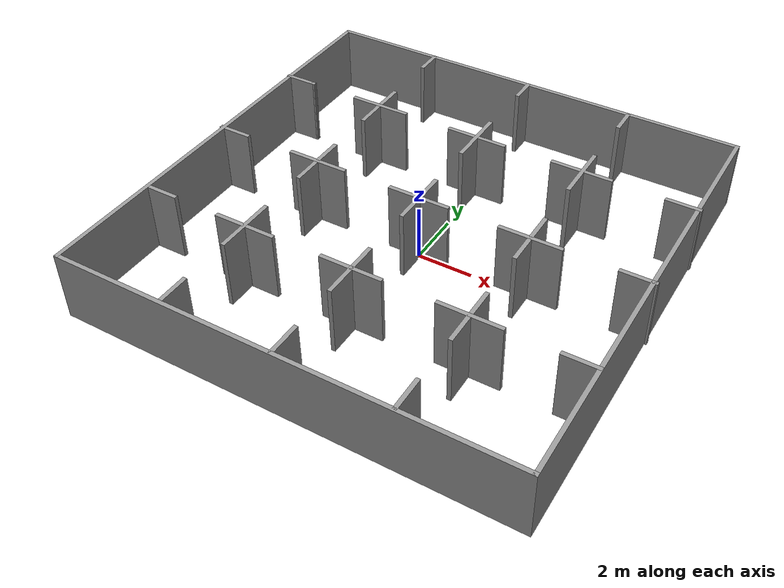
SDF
<?xml version='1.0'?>
<sdf version='1.6'>
  <model name='grid'>
    <link name='Wall_1'>
      <pose frame=''>-0.008852 -8.05426 0 0 -0 0</pose>
      <self_collide>0</self_collide>
      <kinematic>0</kinematic>
      <visual name='Wall_1_Visual'>
        <pose frame=''>0 0 1.25 0 -0 0</pose>
        <geometry>
          <box>
            <size>16.25 0.15 2.5</size>
          </box>
        </geometry>
        <material>
          <script>
            <uri>file://media/materials/scripts/gazebo.material</uri>
            <name>Gazebo/Grey</name>
          </script>
          <ambient>1 1 1 1</ambient>
          <diffuse>0.7 0.7 0.7 1</diffuse>
          <specular>0.01 0.01 0.01 1</specular>
          <emissive>0 0 0 1</emissive>
        </material>
        <cast_shadows>1</cast_shadows>
        <transparency>0</transparency>
      </visual>
      <collision name='Wall_1_Collision'>
        <laser_retro>0</laser_retro>
        <max_contacts>10</max_contacts>
        <pose frame=''>0 0 1.25 0 -0 0</pose>
        <geometry>
          <box>
            <size>16.25 0.15 2.5</size>
          </box>
        </geometry>
        <surface>
          <friction>
            <ode>
              <mu>1</mu>
              <mu2>1</mu2>
              <fdir1>0 0 0</fdir1>
              <slip1>0</slip1>
              <slip2>0</slip2>
            </ode>
            <torsional>
              <coefficient>1</coefficient>
              <patch_radius>0</patch_radius>
              <surface_radius>0</surface_radius>
              <use_patch_radius>1</use_patch_radius>
              <ode>
                <slip>0</slip>
              </ode>
            </torsional>
          </friction>
          <bounce>
            <restitution_coefficient>0</restitution_coefficient>
            <threshold>1e+06</threshold>
          </bounce>
          <contact>
            <collide_without_contact>0</collide_without_contact>
            <collide_without_contact_bitmask>1</collide_without_contact_bitmask>
            <collide_bitmask>1</collide_bitmask>
            <ode>
              <soft_cfm>0</soft_cfm>
              <soft_erp>0.2</soft_erp>
              <kp>1e+13</kp>
              <kd>1</kd>
              <max_vel>0.01</max_vel>
              <min_depth>0</min_depth>
            </ode>
            <bullet>
              <split_impulse>1</split_impulse>
              <split_impulse_penetration_threshold>-0.01</split_impulse_penetration_threshold>
              <soft_cfm>0</soft_cfm>
              <soft_erp>0.2</soft_erp>
              <kp>1e+13</kp>
              <kd>1</kd>
            </bullet>
          </contact>
        </surface>
      </collision>
    </link>
    <link name='Wall_100'>
      <pose frame=''>-4.03249 -4.01202 0 0 -0 0</pose>
      <self_collide>0</self_collide>
      <kinematic>0</kinematic>
      <visual name='Wall_100_Visual'>
        <pose frame=''>0 0 1.25 0 -0 0</pose>
        <geometry>
          <box>
            <size>2.25 0.15 2.5</size>
          </box>
        </geometry>
        <material>
          <script>
            <uri>file://media/materials/scripts/gazebo.material</uri>
            <name>Gazebo/Grey</name>
          </script>
          <ambient>1 1 1 1</ambient>
          <diffuse>0.7 0.7 0.7 1</diffuse>
          <specular>0.01 0.01 0.01 1</specular>
          <emissive>0 0 0 1</emissive>
        </material>
        <cast_shadows>1</cast_shadows>
        <transparency>0</transparency>
      </visual>
      <collision name='Wall_100_Collision'>
        <laser_retro>0</laser_retro>
        <max_contacts>10</max_contacts>
        <pose frame=''>0 0 1.25 0 -0 0</pose>
        <geometry>
          <box>
            <size>2.25 0.15 2.5</size>
          </box>
        </geometry>
        <surface>
          <friction>
            <ode>
              <mu>1</mu>
              <mu2>1</mu2>
              <fdir1>0 0 0</fdir1>
              <slip1>0</slip1>
              <slip2>0</slip2>
            </ode>
            <torsional>
              <coefficient>1</coefficient>
              <patch_radius>0</patch_radius>
              <surface_radius>0</surface_radius>
              <use_patch_radius>1</use_patch_radius>
              <ode>
                <slip>0</slip>
              </ode>
            </torsional>
          </friction>
          <bounce>
            <restitution_coefficient>0</restitution_coefficient>
            <threshold>1e+06</threshold>
          </bounce>
          <contact>
            <collide_without_contact>0</collide_without_contact>
            <collide_without_contact_bitmask>1</collide_without_contact_bitmask>
            <collide_bitmask>1</collide_bitmask>
            <ode>
              <soft_cfm>0</soft_cfm>
              <soft_erp>0.2</soft_erp>
              <kp>1e+13</kp>
              <kd>1</kd>
              <max_vel>0.01</max_vel>
              <min_depth>0</min_depth>
            </ode>
            <bullet>
              <split_impulse>1</split_impulse>
              <split_impulse_penetration_threshold>-0.01</split_impulse_penetration_threshold>
              <soft_cfm>0</soft_cfm>
              <soft_erp>0.2</soft_erp>
              <kp>1e+13</kp>
              <kd>1</kd>
            </bullet>
          </contact>
        </surface>
      </collision>
    </link>
    <link name='Wall_102'>
      <pose frame=''>-0.033055 0.014999 0 0 -0 0</pose>
      <self_collide>0</self_collide>
      <kinematic>0</kinematic>
      <visual name='Wall_102_Visual'>
        <pose frame=''>0 0 1.25 0 -0 0</pose>
        <geometry>
          <box>
            <size>2.25 0.15 2.5</size>
          </box>
        </geometry>
        <material>
          <script>
            <uri>file://media/materials/scripts/gazebo.material</uri>
            <name>Gazebo/Grey</name>
          </script>
          <ambient>1 1 1 1</ambient>
          <diffuse>0.7 0.7 0.7 1</diffuse>
          <specular>0.01 0.01 0.01 1</specular>
          <emissive>0 0 0 1</emissive>
        </material>
        <cast_shadows>1</cast_shadows>
        <transparency>0</transparency>
      </visual>
      <collision name='Wall_102_Collision'>
        <laser_retro>0</laser_retro>
        <max_contacts>10</max_contacts>
        <pose frame=''>0 0 1.25 0 -0 0</pose>
        <geometry>
          <box>
            <size>2.25 0.15 2.5</size>
          </box>
        </geometry>
        <surface>
          <friction>
            <ode>
              <mu>1</mu>
              <mu2>1</mu2>
              <fdir1>0 0 0</fdir1>
              <slip1>0</slip1>
              <slip2>0</slip2>
            </ode>
            <torsional>
              <coefficient>1</coefficient>
              <patch_radius>0</patch_radius>
              <surface_radius>0</surface_radius>
              <use_patch_radius>1</use_patch_radius>
              <ode>
                <slip>0</slip>
              </ode>
            </torsional>
          </friction>
          <bounce>
            <restitution_coefficient>0</restitution_coefficient>
            <threshold>1e+06</threshold>
          </bounce>
          <contact>
            <collide_without_contact>0</collide_without_contact>
            <collide_without_contact_bitmask>1</collide_without_contact_bitmask>
            <collide_bitmask>1</collide_bitmask>
            <ode>
              <soft_cfm>0</soft_cfm>
              <soft_erp>0.2</soft_erp>
              <kp>1e+13</kp>
              <kd>1</kd>
              <max_vel>0.01</max_vel>
              <min_depth>0</min_depth>
            </ode>
            <bullet>
              <split_impulse>1</split_impulse>
              <split_impulse_penetration_threshold>-0.01</split_impulse_penetration_threshold>
              <soft_cfm>0</soft_cfm>
              <soft_erp>0.2</soft_erp>
              <kp>1e+13</kp>
              <kd>1</kd>
            </bullet>
          </contact>
        </surface>
      </collision>
    </link>
    <link name='Wall_104'>
      <pose frame=''>-0.007344 0.003934 0 0 0 -1.5708</pose>
      <self_collide>0</self_collide>
      <kinematic>0</kinematic>
      <visual name='Wall_104_Visual'>
        <pose frame=''>0 0 1.25 0 -0 0</pose>
        <geometry>
          <box>
            <size>2.25 0.15 2.5</size>
          </box>
        </geometry>
        <material>
          <script>
            <uri>file://media/materials/scripts/gazebo.material</uri>
            <name>Gazebo/Grey</name>
          </script>
          <ambient>1 1 1 1</ambient>
          <diffuse>0.7 0.7 0.7 1</diffuse>
          <specular>0.01 0.01 0.01 1</specular>
          <emissive>0 0 0 1</emissive>
        </material>
        <cast_shadows>1</cast_shadows>
        <transparency>0</transparency>
      </visual>
      <collision name='Wall_104_Collision'>
        <laser_retro>0</laser_retro>
        <max_contacts>10</max_contacts>
        <pose frame=''>0 0 1.25 0 -0 0</pose>
        <geometry>
          <box>
            <size>2.25 0.15 2.5</size>
          </box>
        </geometry>
        <surface>
          <friction>
            <ode>
              <mu>1</mu>
              <mu2>1</mu2>
              <fdir1>0 0 0</fdir1>
              <slip1>0</slip1>
              <slip2>0</slip2>
            </ode>
            <torsional>
              <coefficient>1</coefficient>
              <patch_radius>0</patch_radius>
              <surface_radius>0</surface_radius>
              <use_patch_radius>1</use_patch_radius>
              <ode>
                <slip>0</slip>
              </ode>
            </torsional>
          </friction>
          <bounce>
            <restitution_coefficient>0</restitution_coefficient>
            <threshold>1e+06</threshold>
          </bounce>
          <contact>
            <collide_without_contact>0</collide_without_contact>
            <collide_without_contact_bitmask>1</collide_without_contact_bitmask>
            <collide_bitmask>1</collide_bitmask>
            <ode>
              <soft_cfm>0</soft_cfm>
              <soft_erp>0.2</soft_erp>
              <kp>1e+13</kp>
              <kd>1</kd>
              <max_vel>0.01</max_vel>
              <min_depth>0</min_depth>
            </ode>
            <bullet>
              <split_impulse>1</split_impulse>
              <split_impulse_penetration_threshold>-0.01</split_impulse_penetration_threshold>
              <soft_cfm>0</soft_cfm>
              <soft_erp>0.2</soft_erp>
              <kp>1e+13</kp>
              <kd>1</kd>
            </bullet>
          </contact>
        </surface>
      </collision>
    </link>
    <link name='Wall_11'>
      <pose frame=''>-6.98644 4.04261 0 0 -0 0</pose>
      <self_collide>0</self_collide>
      <kinematic>0</kinematic>
      <visual name='Wall_11_Visual'>
        <pose frame=''>0 0 1.25 0 -0 0</pose>
        <geometry>
          <box>
            <size>0.15 0.15 2.5</size>
          </box>
        </geometry>
        <material>
          <script>
            <uri>file://media/materials/scripts/gazebo.material</uri>
            <name>Gazebo/Grey</name>
          </script>
          <ambient>1 1 1 1</ambient>
          <diffuse>0.7 0.7 0.7 1</diffuse>
          <specular>0.01 0.01 0.01 1</specular>
          <emissive>0 0 0 1</emissive>
        </material>
        <cast_shadows>1</cast_shadows>
        <transparency>0</transparency>
      </visual>
      <collision name='Wall_11_Collision'>
        <laser_retro>0</laser_retro>
        <max_contacts>10</max_contacts>
        <pose frame=''>0 0 1.25 0 -0 0</pose>
        <geometry>
          <box>
            <size>0.15 0.15 2.5</size>
          </box>
        </geometry>
        <surface>
          <friction>
            <ode>
              <mu>1</mu>
              <mu2>1</mu2>
              <fdir1>0 0 0</fdir1>
              <slip1>0</slip1>
              <slip2>0</slip2>
            </ode>
            <torsional>
              <coefficient>1</coefficient>
              <patch_radius>0</patch_radius>
              <surface_radius>0</surface_radius>
              <use_patch_radius>1</use_patch_radius>
              <ode>
                <slip>0</slip>
              </ode>
            </torsional>
          </friction>
          <bounce>
            <restitution_coefficient>0</restitution_coefficient>
            <threshold>1e+06</threshold>
          </bounce>
          <contact>
            <collide_without_contact>0</collide_without_contact>
            <collide_without_contact_bitmask>1</collide_without_contact_bitmask>
            <collide_bitmask>1</collide_bitmask>
            <ode>
              <soft_cfm>0</soft_cfm>
              <soft_erp>0.2</soft_erp>
              <kp>1e+13</kp>
              <kd>1</kd>
              <max_vel>0.01</max_vel>
              <min_depth>0</min_depth>
            </ode>
            <bullet>
              <split_impulse>1</split_impulse>
              <split_impulse_penetration_threshold>-0.01</split_impulse_penetration_threshold>
              <soft_cfm>0</soft_cfm>
              <soft_erp>0.2</soft_erp>
              <kp>1e+13</kp>
              <kd>1</kd>
            </bullet>
          </contact>
        </surface>
      </collision>
    </link>
    <link name='Wall_15'>
      <pose frame=''>-7.5627 0.013696 0 0 -0 0</pose>
      <self_collide>0</self_collide>
      <kinematic>0</kinematic>
      <visual name='Wall_15_Visual'>
        <pose frame=''>0 0 1.25 0 -0 0</pose>
        <geometry>
          <box>
            <size>1.25 0.15 2.5</size>
          </box>
        </geometry>
        <material>
          <script>
            <uri>file://media/materials/scripts/gazebo.material</uri>
            <name>Gazebo/Grey</name>
          </script>
          <ambient>1 1 1 1</ambient>
          <diffuse>0.7 0.7 0.7 1</diffuse>
          <specular>0.01 0.01 0.01 1</specular>
          <emissive>0 0 0 1</emissive>
        </material>
        <cast_shadows>1</cast_shadows>
        <transparency>0</transparency>
      </visual>
      <collision name='Wall_15_Collision'>
        <laser_retro>0</laser_retro>
        <max_contacts>10</max_contacts>
        <pose frame=''>0 0 1.25 0 -0 0</pose>
        <geometry>
          <box>
            <size>1.25 0.15 2.5</size>
          </box>
        </geometry>
        <surface>
          <friction>
            <ode>
              <mu>1</mu>
              <mu2>1</mu2>
              <fdir1>0 0 0</fdir1>
              <slip1>0</slip1>
              <slip2>0</slip2>
            </ode>
            <torsional>
              <coefficient>1</coefficient>
              <patch_radius>0</patch_radius>
              <surface_radius>0</surface_radius>
              <use_patch_radius>1</use_patch_radius>
              <ode>
                <slip>0</slip>
              </ode>
            </torsional>
          </friction>
          <bounce>
            <restitution_coefficient>0</restitution_coefficient>
            <threshold>1e+06</threshold>
          </bounce>
          <contact>
            <collide_without_contact>0</collide_without_contact>
            <collide_without_contact_bitmask>1</collide_without_contact_bitmask>
            <collide_bitmask>1</collide_bitmask>
            <ode>
              <soft_cfm>0</soft_cfm>
              <soft_erp>0.2</soft_erp>
              <kp>1e+13</kp>
              <kd>1</kd>
              <max_vel>0.01</max_vel>
              <min_depth>0</min_depth>
            </ode>
            <bullet>
              <split_impulse>1</split_impulse>
              <split_impulse_penetration_threshold>-0.01</split_impulse_penetration_threshold>
              <soft_cfm>0</soft_cfm>
              <soft_erp>0.2</soft_erp>
              <kp>1e+13</kp>
              <kd>1</kd>
            </bullet>
          </contact>
        </surface>
      </collision>
    </link>
    <link name='Wall_2'>
      <pose frame=''>8.04115 -0.004256 0 0 -0 1.5708</pose>
      <self_collide>0</self_collide>
      <kinematic>0</kinematic>
      <visual name='Wall_2_Visual'>
        <pose frame=''>0 0 1.25 0 -0 0</pose>
        <geometry>
          <box>
            <size>16.25 0.15 2.5</size>
          </box>
        </geometry>
        <material>
          <script>
            <uri>file://media/materials/scripts/gazebo.material</uri>
            <name>Gazebo/Grey</name>
          </script>
          <ambient>1 1 1 1</ambient>
          <diffuse>0.7 0.7 0.7 1</diffuse>
          <specular>0.01 0.01 0.01 1</specular>
          <emissive>0 0 0 1</emissive>
        </material>
        <cast_shadows>1</cast_shadows>
        <transparency>0</transparency>
      </visual>
      <collision name='Wall_2_Collision'>
        <laser_retro>0</laser_retro>
        <max_contacts>10</max_contacts>
        <pose frame=''>0 0 1.25 0 -0 0</pose>
        <geometry>
          <box>
            <size>16.25 0.15 2.5</size>
          </box>
        </geometry>
        <surface>
          <friction>
            <ode>
              <mu>1</mu>
              <mu2>1</mu2>
              <fdir1>0 0 0</fdir1>
              <slip1>0</slip1>
              <slip2>0</slip2>
            </ode>
            <torsional>
              <coefficient>1</coefficient>
              <patch_radius>0</patch_radius>
              <surface_radius>0</surface_radius>
              <use_patch_radius>1</use_patch_radius>
              <ode>
                <slip>0</slip>
              </ode>
            </torsional>
          </friction>
          <bounce>
            <restitution_coefficient>0</restitution_coefficient>
            <threshold>1e+06</threshold>
          </bounce>
          <contact>
            <collide_without_contact>0</collide_without_contact>
            <collide_without_contact_bitmask>1</collide_without_contact_bitmask>
            <collide_bitmask>1</collide_bitmask>
            <ode>
              <soft_cfm>0</soft_cfm>
              <soft_erp>0.2</soft_erp>
              <kp>1e+13</kp>
              <kd>1</kd>
              <max_vel>0.01</max_vel>
              <min_depth>0</min_depth>
            </ode>
            <bullet>
              <split_impulse>1</split_impulse>
              <split_impulse_penetration_threshold>-0.01</split_impulse_penetration_threshold>
              <soft_cfm>0</soft_cfm>
              <soft_erp>0.2</soft_erp>
              <kp>1e+13</kp>
              <kd>1</kd>
            </bullet>
          </contact>
        </surface>
      </collision>
    </link>
    <link name='Wall_21'>
      <pose frame=''>-0.027047 3.99209 0 0 0 -1.5708</pose>
      <self_collide>0</self_collide>
      <kinematic>0</kinematic>
      <visual name='Wall_21_Visual'>
        <pose frame=''>0 0 1.25 0 -0 0</pose>
        <geometry>
          <box>
            <size>2.25 0.15 2.5</size>
          </box>
        </geometry>
        <material>
          <script>
            <uri>file://media/materials/scripts/gazebo.material</uri>
            <name>Gazebo/Grey</name>
          </script>
          <ambient>1 1 1 1</ambient>
          <diffuse>0.7 0.7 0.7 1</diffuse>
          <specular>0.01 0.01 0.01 1</specular>
          <emissive>0 0 0 1</emissive>
        </material>
        <cast_shadows>1</cast_shadows>
        <transparency>0</transparency>
      </visual>
      <collision name='Wall_21_Collision'>
        <laser_retro>0</laser_retro>
        <max_contacts>10</max_contacts>
        <pose frame=''>0 0 1.25 0 -0 0</pose>
        <geometry>
          <box>
            <size>2.25 0.15 2.5</size>
          </box>
        </geometry>
        <surface>
          <friction>
            <ode>
              <mu>1</mu>
              <mu2>1</mu2>
              <fdir1>0 0 0</fdir1>
              <slip1>0</slip1>
              <slip2>0</slip2>
            </ode>
            <torsional>
              <coefficient>1</coefficient>
              <patch_radius>0</patch_radius>
              <surface_radius>0</surface_radius>
              <use_patch_radius>1</use_patch_radius>
              <ode>
                <slip>0</slip>
              </ode>
            </torsional>
          </friction>
          <bounce>
            <restitution_coefficient>0</restitution_coefficient>
            <threshold>1e+06</threshold>
          </bounce>
          <contact>
            <collide_without_contact>0</collide_without_contact>
            <collide_without_contact_bitmask>1</collide_without_contact_bitmask>
            <collide_bitmask>1</collide_bitmask>
            <ode>
              <soft_cfm>0</soft_cfm>
              <soft_erp>0.2</soft_erp>
              <kp>1e+13</kp>
              <kd>1</kd>
              <max_vel>0.01</max_vel>
              <min_depth>0</min_depth>
            </ode>
            <bullet>
              <split_impulse>1</split_impulse>
              <split_impulse_penetration_threshold>-0.01</split_impulse_penetration_threshold>
              <soft_cfm>0</soft_cfm>
              <soft_erp>0.2</soft_erp>
              <kp>1e+13</kp>
              <kd>1</kd>
            </bullet>
          </contact>
        </surface>
      </collision>
    </link>
    <link name='Wall_23'>
      <pose frame=''>-0.019757 4.0163 0 0 -0 0</pose>
      <self_collide>0</self_collide>
      <kinematic>0</kinematic>
      <visual name='Wall_23_Visual'>
        <pose frame=''>0 0 1.25 0 -0 0</pose>
        <geometry>
          <box>
            <size>2.25 0.15 2.5</size>
          </box>
        </geometry>
        <material>
          <script>
            <uri>file://media/materials/scripts/gazebo.material</uri>
            <name>Gazebo/Grey</name>
          </script>
          <ambient>1 1 1 1</ambient>
          <diffuse>0.7 0.7 0.7 1</diffuse>
          <specular>0.01 0.01 0.01 1</specular>
          <emissive>0 0 0 1</emissive>
        </material>
        <cast_shadows>1</cast_shadows>
        <transparency>0</transparency>
      </visual>
      <collision name='Wall_23_Collision'>
        <laser_retro>0</laser_retro>
        <max_contacts>10</max_contacts>
        <pose frame=''>0 0 1.25 0 -0 0</pose>
        <geometry>
          <box>
            <size>2.25 0.15 2.5</size>
          </box>
        </geometry>
        <surface>
          <friction>
            <ode>
              <mu>1</mu>
              <mu2>1</mu2>
              <fdir1>0 0 0</fdir1>
              <slip1>0</slip1>
              <slip2>0</slip2>
            </ode>
            <torsional>
              <coefficient>1</coefficient>
              <patch_radius>0</patch_radius>
              <surface_radius>0</surface_radius>
              <use_patch_radius>1</use_patch_radius>
              <ode>
                <slip>0</slip>
              </ode>
            </torsional>
          </friction>
          <bounce>
            <restitution_coefficient>0</restitution_coefficient>
            <threshold>1e+06</threshold>
          </bounce>
          <contact>
            <collide_without_contact>0</collide_without_contact>
            <collide_without_contact_bitmask>1</collide_without_contact_bitmask>
            <collide_bitmask>1</collide_bitmask>
            <ode>
              <soft_cfm>0</soft_cfm>
              <soft_erp>0.2</soft_erp>
              <kp>1e+13</kp>
              <kd>1</kd>
              <max_vel>0.01</max_vel>
              <min_depth>0</min_depth>
            </ode>
            <bullet>
              <split_impulse>1</split_impulse>
              <split_impulse_penetration_threshold>-0.01</split_impulse_penetration_threshold>
              <soft_cfm>0</soft_cfm>
              <soft_erp>0.2</soft_erp>
              <kp>1e+13</kp>
              <kd>1</kd>
            </bullet>
          </contact>
        </surface>
      </collision>
    </link>
    <link name='Wall_25'>
      <pose frame=''>3.99567 3.97198 0 0 0 -1.5708</pose>
      <self_collide>0</self_collide>
      <kinematic>0</kinematic>
      <visual name='Wall_25_Visual'>
        <pose frame=''>0 0 1.25 0 -0 0</pose>
        <geometry>
          <box>
            <size>2.25 0.15 2.5</size>
          </box>
        </geometry>
        <material>
          <script>
            <uri>file://media/materials/scripts/gazebo.material</uri>
            <name>Gazebo/Grey</name>
          </script>
          <ambient>1 1 1 1</ambient>
          <diffuse>0.7 0.7 0.7 1</diffuse>
          <specular>0.01 0.01 0.01 1</specular>
          <emissive>0 0 0 1</emissive>
        </material>
        <cast_shadows>1</cast_shadows>
        <transparency>0</transparency>
      </visual>
      <collision name='Wall_25_Collision'>
        <laser_retro>0</laser_retro>
        <max_contacts>10</max_contacts>
        <pose frame=''>0 0 1.25 0 -0 0</pose>
        <geometry>
          <box>
            <size>2.25 0.15 2.5</size>
          </box>
        </geometry>
        <surface>
          <friction>
            <ode>
              <mu>1</mu>
              <mu2>1</mu2>
              <fdir1>0 0 0</fdir1>
              <slip1>0</slip1>
              <slip2>0</slip2>
            </ode>
            <torsional>
              <coefficient>1</coefficient>
              <patch_radius>0</patch_radius>
              <surface_radius>0</surface_radius>
              <use_patch_radius>1</use_patch_radius>
              <ode>
                <slip>0</slip>
              </ode>
            </torsional>
          </friction>
          <bounce>
            <restitution_coefficient>0</restitution_coefficient>
            <threshold>1e+06</threshold>
          </bounce>
          <contact>
            <collide_without_contact>0</collide_without_contact>
            <collide_without_contact_bitmask>1</collide_without_contact_bitmask>
            <collide_bitmask>1</collide_bitmask>
            <ode>
              <soft_cfm>0</soft_cfm>
              <soft_erp>0.2</soft_erp>
              <kp>1e+13</kp>
              <kd>1</kd>
              <max_vel>0.01</max_vel>
              <min_depth>0</min_depth>
            </ode>
            <bullet>
              <split_impulse>1</split_impulse>
              <split_impulse_penetration_threshold>-0.01</split_impulse_penetration_threshold>
              <soft_cfm>0</soft_cfm>
              <soft_erp>0.2</soft_erp>
              <kp>1e+13</kp>
              <kd>1</kd>
            </bullet>
          </contact>
        </surface>
      </collision>
    </link>
    <link name='Wall_29'>
      <pose frame=''>7.54259 3.99618 0 0 -0 0</pose>
      <self_collide>0</self_collide>
      <kinematic>0</kinematic>
      <visual name='Wall_29_Visual'>
        <pose frame=''>0 0 1.25 0 -0 0</pose>
        <geometry>
          <box>
            <size>1.25 0.15 2.5</size>
          </box>
        </geometry>
        <material>
          <script>
            <uri>file://media/materials/scripts/gazebo.material</uri>
            <name>Gazebo/Grey</name>
          </script>
          <ambient>1 1 1 1</ambient>
          <diffuse>0.7 0.7 0.7 1</diffuse>
          <specular>0.01 0.01 0.01 1</specular>
          <emissive>0 0 0 1</emissive>
        </material>
        <cast_shadows>1</cast_shadows>
        <transparency>0</transparency>
      </visual>
      <collision name='Wall_29_Collision'>
        <laser_retro>0</laser_retro>
        <max_contacts>10</max_contacts>
        <pose frame=''>0 0 1.25 0 -0 0</pose>
        <geometry>
          <box>
            <size>1.25 0.15 2.5</size>
          </box>
        </geometry>
        <surface>
          <friction>
            <ode>
              <mu>1</mu>
              <mu2>1</mu2>
              <fdir1>0 0 0</fdir1>
              <slip1>0</slip1>
              <slip2>0</slip2>
            </ode>
            <torsional>
              <coefficient>1</coefficient>
              <patch_radius>0</patch_radius>
              <surface_radius>0</surface_radius>
              <use_patch_radius>1</use_patch_radius>
              <ode>
                <slip>0</slip>
              </ode>
            </torsional>
          </friction>
          <bounce>
            <restitution_coefficient>0</restitution_coefficient>
            <threshold>1e+06</threshold>
          </bounce>
          <contact>
            <collide_without_contact>0</collide_without_contact>
            <collide_without_contact_bitmask>1</collide_without_contact_bitmask>
            <collide_bitmask>1</collide_bitmask>
            <ode>
              <soft_cfm>0</soft_cfm>
              <soft_erp>0.2</soft_erp>
              <kp>1e+13</kp>
              <kd>1</kd>
              <max_vel>0.01</max_vel>
              <min_depth>0</min_depth>
            </ode>
            <bullet>
              <split_impulse>1</split_impulse>
              <split_impulse_penetration_threshold>-0.01</split_impulse_penetration_threshold>
              <soft_cfm>0</soft_cfm>
              <soft_erp>0.2</soft_erp>
              <kp>1e+13</kp>
              <kd>1</kd>
            </bullet>
          </contact>
        </surface>
      </collision>
    </link>
    <link name='Wall_3'>
      <pose frame=''>-0.008852 8.04574 0 0 -0 3.14159</pose>
      <self_collide>0</self_collide>
      <kinematic>0</kinematic>
      <visual name='Wall_3_Visual'>
        <pose frame=''>0 0 1.25 0 -0 0</pose>
        <geometry>
          <box>
            <size>16.25 0.15 2.5</size>
          </box>
        </geometry>
        <material>
          <script>
            <uri>file://media/materials/scripts/gazebo.material</uri>
            <name>Gazebo/Grey</name>
          </script>
          <ambient>1 1 1 1</ambient>
          <diffuse>0.7 0.7 0.7 1</diffuse>
          <specular>0.01 0.01 0.01 1</specular>
          <emissive>0 0 0 1</emissive>
        </material>
        <cast_shadows>1</cast_shadows>
        <transparency>0</transparency>
      </visual>
      <collision name='Wall_3_Collision'>
        <laser_retro>0</laser_retro>
        <max_contacts>10</max_contacts>
        <pose frame=''>0 0 1.25 0 -0 0</pose>
        <geometry>
          <box>
            <size>16.25 0.15 2.5</size>
          </box>
        </geometry>
        <surface>
          <friction>
            <ode>
              <mu>1</mu>
              <mu2>1</mu2>
              <fdir1>0 0 0</fdir1>
              <slip1>0</slip1>
              <slip2>0</slip2>
            </ode>
            <torsional>
              <coefficient>1</coefficient>
              <patch_radius>0</patch_radius>
              <surface_radius>0</surface_radius>
              <use_patch_radius>1</use_patch_radius>
              <ode>
                <slip>0</slip>
              </ode>
            </torsional>
          </friction>
          <bounce>
            <restitution_coefficient>0</restitution_coefficient>
            <threshold>1e+06</threshold>
          </bounce>
          <contact>
            <collide_without_contact>0</collide_without_contact>
            <collide_without_contact_bitmask>1</collide_without_contact_bitmask>
            <collide_bitmask>1</collide_bitmask>
            <ode>
              <soft_cfm>0</soft_cfm>
              <soft_erp>0.2</soft_erp>
              <kp>1e+13</kp>
              <kd>1</kd>
              <max_vel>0.01</max_vel>
              <min_depth>0</min_depth>
            </ode>
            <bullet>
              <split_impulse>1</split_impulse>
              <split_impulse_penetration_threshold>-0.01</split_impulse_penetration_threshold>
              <soft_cfm>0</soft_cfm>
              <soft_erp>0.2</soft_erp>
              <kp>1e+13</kp>
              <kd>1</kd>
            </bullet>
          </contact>
        </surface>
      </collision>
    </link>
    <link name='Wall_4'>
      <pose frame=''>-8.05885 -0.004256 0 0 0 -1.5708</pose>
      <self_collide>0</self_collide>
      <kinematic>0</kinematic>
      <visual name='Wall_4_Visual'>
        <pose frame=''>0 0 1.25 0 -0 0</pose>
        <geometry>
          <box>
            <size>16.25 0.15 2.5</size>
          </box>
        </geometry>
        <material>
          <script>
            <uri>file://media/materials/scripts/gazebo.material</uri>
            <name>Gazebo/Grey</name>
          </script>
          <ambient>1 1 1 1</ambient>
          <diffuse>0.7 0.7 0.7 1</diffuse>
          <specular>0.01 0.01 0.01 1</specular>
          <emissive>0 0 0 1</emissive>
        </material>
        <cast_shadows>1</cast_shadows>
        <transparency>0</transparency>
      </visual>
      <collision name='Wall_4_Collision'>
        <laser_retro>0</laser_retro>
        <max_contacts>10</max_contacts>
        <pose frame=''>0 0 1.25 0 -0 0</pose>
        <geometry>
          <box>
            <size>16.25 0.15 2.5</size>
          </box>
        </geometry>
        <surface>
          <friction>
            <ode>
              <mu>1</mu>
              <mu2>1</mu2>
              <fdir1>0 0 0</fdir1>
              <slip1>0</slip1>
              <slip2>0</slip2>
            </ode>
            <torsional>
              <coefficient>1</coefficient>
              <patch_radius>0</patch_radius>
              <surface_radius>0</surface_radius>
              <use_patch_radius>1</use_patch_radius>
              <ode>
                <slip>0</slip>
              </ode>
            </torsional>
          </friction>
          <bounce>
            <restitution_coefficient>0</restitution_coefficient>
            <threshold>1e+06</threshold>
          </bounce>
          <contact>
            <collide_without_contact>0</collide_without_contact>
            <collide_without_contact_bitmask>1</collide_without_contact_bitmask>
            <collide_bitmask>1</collide_bitmask>
            <ode>
              <soft_cfm>0</soft_cfm>
              <soft_erp>0.2</soft_erp>
              <kp>1e+13</kp>
              <kd>1</kd>
              <max_vel>0.01</max_vel>
              <min_depth>0</min_depth>
            </ode>
            <bullet>
              <split_impulse>1</split_impulse>
              <split_impulse_penetration_threshold>-0.01</split_impulse_penetration_threshold>
              <soft_cfm>0</soft_cfm>
              <soft_erp>0.2</soft_erp>
              <kp>1e+13</kp>
              <kd>1</kd>
            </bullet>
          </contact>
        </surface>
      </collision>
    </link>
    <link name='Wall_46'>
      <pose frame=''>4.00578 -0.000512 0 0 0 -1.5708</pose>
      <self_collide>0</self_collide>
      <kinematic>0</kinematic>
      <gravity>1</gravity>
      <inertial>
        <mass>1</mass>
        <pose frame=''>0 0 0 0 -0 0</pose>
        <inertia>
          <ixx>1</ixx>
          <ixy>0</ixy>
          <ixz>0</ixz>
          <iyy>1</iyy>
          <iyz>0</iyz>
          <izz>1</izz>
        </inertia>
      </inertial>
      <visual name='Wall_46_Visual'>
        <pose frame=''>0 0 1.25 0 -0 0</pose>
        <geometry>
          <box>
            <size>2.25 0.15 2.5</size>
          </box>
        </geometry>
        <material>
          <script>
            <uri>file://media/materials/scripts/gazebo.material</uri>
            <name>Gazebo/Grey</name>
          </script>
          <ambient>1 1 1 1</ambient>
          <diffuse>0.7 0.7 0.7 1</diffuse>
          <specular>0.01 0.01 0.01 1</specular>
          <emissive>0 0 0 1</emissive>
          <shader type='vertex'>
            <normal_map>__default__</normal_map>
          </shader>
        </material>
        <cast_shadows>1</cast_shadows>
        <transparency>0</transparency>
      </visual>
      <collision name='Wall_46_Collision'>
        <laser_retro>0</laser_retro>
        <max_contacts>10</max_contacts>
        <pose frame=''>0 0 1.25 0 -0 0</pose>
        <geometry>
          <box>
            <size>2.25 0.15 2.5</size>
          </box>
        </geometry>
        <surface>
          <friction>
            <ode>
              <mu>1</mu>
              <mu2>1</mu2>
              <fdir1>0 0 0</fdir1>
              <slip1>0</slip1>
              <slip2>0</slip2>
            </ode>
            <torsional>
              <coefficient>1</coefficient>
              <patch_radius>0</patch_radius>
              <surface_radius>0</surface_radius>
              <use_patch_radius>1</use_patch_radius>
              <ode>
                <slip>0</slip>
              </ode>
            </torsional>
          </friction>
          <bounce>
            <restitution_coefficient>0</restitution_coefficient>
            <threshold>1e+06</threshold>
          </bounce>
          <contact>
            <collide_without_contact>0</collide_without_contact>
            <collide_without_contact_bitmask>1</collide_without_contact_bitmask>
            <collide_bitmask>1</collide_bitmask>
            <ode>
              <soft_cfm>0</soft_cfm>
              <soft_erp>0.2</soft_erp>
              <kp>1e+13</kp>
              <kd>1</kd>
              <max_vel>0.01</max_vel>
              <min_depth>0</min_depth>
            </ode>
            <bullet>
              <split_impulse>1</split_impulse>
              <split_impulse_penetration_threshold>-0.01</split_impulse_penetration_threshold>
              <soft_cfm>0</soft_cfm>
              <soft_erp>0.2</soft_erp>
              <kp>1e+13</kp>
              <kd>1</kd>
            </bullet>
          </contact>
        </surface>
      </collision>
    </link>
    <link name='Wall_48'>
      <pose frame=''>4.0001 0 0 0 -0 0</pose>
      <self_collide>0</self_collide>
      <kinematic>0</kinematic>
      <gravity>1</gravity>
      <inertial>
        <mass>1</mass>
        <pose frame=''>0 0 0 0 -0 0</pose>
        <inertia>
          <ixx>1</ixx>
          <ixy>0</ixy>
          <ixz>0</ixz>
          <iyy>1</iyy>
          <iyz>0</iyz>
          <izz>1</izz>
        </inertia>
      </inertial>
      <visual name='Wall_48_Visual'>
        <pose frame=''>0 0 1.25 0 -0 0</pose>
        <geometry>
          <box>
            <size>2.25 0.15 2.5</size>
          </box>
        </geometry>
        <material>
          <script>
            <uri>file://media/materials/scripts/gazebo.material</uri>
            <name>Gazebo/Grey</name>
          </script>
          <ambient>1 1 1 1</ambient>
          <diffuse>0.7 0.7 0.7 1</diffuse>
          <specular>0.01 0.01 0.01 1</specular>
          <emissive>0 0 0 1</emissive>
          <shader type='vertex'>
            <normal_map>__default__</normal_map>
          </shader>
        </material>
        <cast_shadows>1</cast_shadows>
        <transparency>0</transparency>
      </visual>
      <collision name='Wall_48_Collision'>
        <laser_retro>0</laser_retro>
        <max_contacts>10</max_contacts>
        <pose frame=''>0 0 1.25 0 -0 0</pose>
        <geometry>
          <box>
            <size>2.25 0.15 2.5</size>
          </box>
        </geometry>
        <surface>
          <friction>
            <ode>
              <mu>1</mu>
              <mu2>1</mu2>
              <fdir1>0 0 0</fdir1>
              <slip1>0</slip1>
              <slip2>0</slip2>
            </ode>
            <torsional>
              <coefficient>1</coefficient>
              <patch_radius>0</patch_radius>
              <surface_radius>0</surface_radius>
              <use_patch_radius>1</use_patch_radius>
              <ode>
                <slip>0</slip>
              </ode>
            </torsional>
          </friction>
          <bounce>
            <restitution_coefficient>0</restitution_coefficient>
            <threshold>1e+06</threshold>
          </bounce>
          <contact>
            <collide_without_contact>0</collide_without_contact>
            <collide_without_contact_bitmask>1</collide_without_contact_bitmask>
            <collide_bitmask>1</collide_bitmask>
            <ode>
              <soft_cfm>0</soft_cfm>
              <soft_erp>0.2</soft_erp>
              <kp>1e+13</kp>
              <kd>1</kd>
              <max_vel>0.01</max_vel>
              <min_depth>0</min_depth>
            </ode>
            <bullet>
              <split_impulse>1</split_impulse>
              <split_impulse_penetration_threshold>-0.01</split_impulse_penetration_threshold>
              <soft_cfm>0</soft_cfm>
              <soft_erp>0.2</soft_erp>
              <kp>1e+13</kp>
              <kd>1</kd>
            </bullet>
          </contact>
        </surface>
      </collision>
    </link>
    <link name='Wall_50'>
      <pose frame=''>7.5627 -0.006418 0 0 -0 0</pose>
      <self_collide>0</self_collide>
      <kinematic>0</kinematic>
      <visual name='Wall_50_Visual'>
        <pose frame=''>0 0 1.25 0 -0 0</pose>
        <geometry>
          <box>
            <size>1.25 0.15 2.5</size>
          </box>
        </geometry>
        <material>
          <script>
            <uri>file://media/materials/scripts/gazebo.material</uri>
            <name>Gazebo/Grey</name>
          </script>
          <ambient>1 1 1 1</ambient>
          <diffuse>0.7 0.7 0.7 1</diffuse>
          <specular>0.01 0.01 0.01 1</specular>
          <emissive>0 0 0 1</emissive>
        </material>
        <cast_shadows>1</cast_shadows>
        <transparency>0</transparency>
      </visual>
      <collision name='Wall_50_Collision'>
        <laser_retro>0</laser_retro>
        <max_contacts>10</max_contacts>
        <pose frame=''>0 0 1.25 0 -0 0</pose>
        <geometry>
          <box>
            <size>1.25 0.15 2.5</size>
          </box>
        </geometry>
        <surface>
          <friction>
            <ode>
              <mu>1</mu>
              <mu2>1</mu2>
              <fdir1>0 0 0</fdir1>
              <slip1>0</slip1>
              <slip2>0</slip2>
            </ode>
            <torsional>
              <coefficient>1</coefficient>
              <patch_radius>0</patch_radius>
              <surface_radius>0</surface_radius>
              <use_patch_radius>1</use_patch_radius>
              <ode>
                <slip>0</slip>
              </ode>
            </torsional>
          </friction>
          <bounce>
            <restitution_coefficient>0</restitution_coefficient>
            <threshold>1e+06</threshold>
          </bounce>
          <contact>
            <collide_without_contact>0</collide_without_contact>
            <collide_without_contact_bitmask>1</collide_without_contact_bitmask>
            <collide_bitmask>1</collide_bitmask>
            <ode>
              <soft_cfm>0</soft_cfm>
              <soft_erp>0.2</soft_erp>
              <kp>1e+13</kp>
              <kd>1</kd>
              <max_vel>0.01</max_vel>
              <min_depth>0</min_depth>
            </ode>
            <bullet>
              <split_impulse>1</split_impulse>
              <split_impulse_penetration_threshold>-0.01</split_impulse_penetration_threshold>
              <soft_cfm>0</soft_cfm>
              <soft_erp>0.2</soft_erp>
              <kp>1e+13</kp>
              <kd>1</kd>
            </bullet>
          </contact>
        </surface>
      </collision>
    </link>
    <link name='Wall_52'>
      <pose frame=''>-7.53951 4.03951 0 0 -0 0.005602</pose>
      <self_collide>0</self_collide>
      <kinematic>0</kinematic>
      <visual name='Wall_52_Visual'>
        <pose frame=''>0 0 1.25 0 -0 0</pose>
        <geometry>
          <box>
            <size>1.25617 0.15 2.5</size>
          </box>
        </geometry>
        <material>
          <script>
            <uri>file://media/materials/scripts/gazebo.material</uri>
            <name>Gazebo/Grey</name>
          </script>
          <ambient>1 1 1 1</ambient>
          <diffuse>0.7 0.7 0.7 1</diffuse>
          <specular>0.01 0.01 0.01 1</specular>
          <emissive>0 0 0 1</emissive>
        </material>
        <cast_shadows>1</cast_shadows>
        <transparency>0</transparency>
      </visual>
      <collision name='Wall_52_Collision'>
        <laser_retro>0</laser_retro>
        <max_contacts>10</max_contacts>
        <pose frame=''>0 0 1.25 0 -0 0</pose>
        <geometry>
          <box>
            <size>1.25617 0.15 2.5</size>
          </box>
        </geometry>
        <surface>
          <friction>
            <ode>
              <mu>1</mu>
              <mu2>1</mu2>
              <fdir1>0 0 0</fdir1>
              <slip1>0</slip1>
              <slip2>0</slip2>
            </ode>
            <torsional>
              <coefficient>1</coefficient>
              <patch_radius>0</patch_radius>
              <surface_radius>0</surface_radius>
              <use_patch_radius>1</use_patch_radius>
              <ode>
                <slip>0</slip>
              </ode>
            </torsional>
          </friction>
          <bounce>
            <restitution_coefficient>0</restitution_coefficient>
            <threshold>1e+06</threshold>
          </bounce>
          <contact>
            <collide_without_contact>0</collide_without_contact>
            <collide_without_contact_bitmask>1</collide_without_contact_bitmask>
            <collide_bitmask>1</collide_bitmask>
            <ode>
              <soft_cfm>0</soft_cfm>
              <soft_erp>0.2</soft_erp>
              <kp>1e+13</kp>
              <kd>1</kd>
              <max_vel>0.01</max_vel>
              <min_depth>0</min_depth>
            </ode>
            <bullet>
              <split_impulse>1</split_impulse>
              <split_impulse_penetration_threshold>-0.01</split_impulse_penetration_threshold>
              <soft_cfm>0</soft_cfm>
              <soft_erp>0.2</soft_erp>
              <kp>1e+13</kp>
              <kd>1</kd>
            </bullet>
          </contact>
        </surface>
      </collision>
    </link>
    <link name='Wall_54'>
      <pose frame=''>-4.02965 7.5939 0 0 0 -1.5708</pose>
      <self_collide>0</self_collide>
      <kinematic>0</kinematic>
      <visual name='Wall_54_Visual'>
        <pose frame=''>0 0 1.25 0 -0 0</pose>
        <geometry>
          <box>
            <size>1 0.15 2.5</size>
          </box>
        </geometry>
        <material>
          <script>
            <uri>file://media/materials/scripts/gazebo.material</uri>
            <name>Gazebo/Grey</name>
          </script>
          <ambient>1 1 1 1</ambient>
          <diffuse>0.7 0.7 0.7 1</diffuse>
          <specular>0.01 0.01 0.01 1</specular>
          <emissive>0 0 0 1</emissive>
        </material>
        <cast_shadows>1</cast_shadows>
        <transparency>0</transparency>
      </visual>
      <collision name='Wall_54_Collision'>
        <laser_retro>0</laser_retro>
        <max_contacts>10</max_contacts>
        <pose frame=''>0 0 1.25 0 -0 0</pose>
        <geometry>
          <box>
            <size>1 0.15 2.5</size>
          </box>
        </geometry>
        <surface>
          <friction>
            <ode>
              <mu>1</mu>
              <mu2>1</mu2>
              <fdir1>0 0 0</fdir1>
              <slip1>0</slip1>
              <slip2>0</slip2>
            </ode>
            <torsional>
              <coefficient>1</coefficient>
              <patch_radius>0</patch_radius>
              <surface_radius>0</surface_radius>
              <use_patch_radius>1</use_patch_radius>
              <ode>
                <slip>0</slip>
              </ode>
            </torsional>
          </friction>
          <bounce>
            <restitution_coefficient>0</restitution_coefficient>
            <threshold>1e+06</threshold>
          </bounce>
          <contact>
            <collide_without_contact>0</collide_without_contact>
            <collide_without_contact_bitmask>1</collide_without_contact_bitmask>
            <collide_bitmask>1</collide_bitmask>
            <ode>
              <soft_cfm>0</soft_cfm>
              <soft_erp>0.2</soft_erp>
              <kp>1e+13</kp>
              <kd>1</kd>
              <max_vel>0.01</max_vel>
              <min_depth>0</min_depth>
            </ode>
            <bullet>
              <split_impulse>1</split_impulse>
              <split_impulse_penetration_threshold>-0.01</split_impulse_penetration_threshold>
              <soft_cfm>0</soft_cfm>
              <soft_erp>0.2</soft_erp>
              <kp>1e+13</kp>
              <kd>1</kd>
            </bullet>
          </contact>
        </surface>
      </collision>
    </link>
    <link name='Wall_57'>
      <pose frame=''>3.95953 4.03641 0 0 -0 0</pose>
      <self_collide>0</self_collide>
      <kinematic>0</kinematic>
      <visual name='Wall_57_Visual'>
        <pose frame=''>0 0 1.25 0 -0 0</pose>
        <geometry>
          <box>
            <size>2.25 0.15 2.5</size>
          </box>
        </geometry>
        <material>
          <script>
            <uri>file://media/materials/scripts/gazebo.material</uri>
            <name>Gazebo/Grey</name>
          </script>
          <ambient>1 1 1 1</ambient>
          <diffuse>0.7 0.7 0.7 1</diffuse>
          <specular>0.01 0.01 0.01 1</specular>
          <emissive>0 0 0 1</emissive>
        </material>
        <cast_shadows>1</cast_shadows>
        <transparency>0</transparency>
      </visual>
      <collision name='Wall_57_Collision'>
        <laser_retro>0</laser_retro>
        <max_contacts>10</max_contacts>
        <pose frame=''>0 0 1.25 0 -0 0</pose>
        <geometry>
          <box>
            <size>2.25 0.15 2.5</size>
          </box>
        </geometry>
        <surface>
          <friction>
            <ode>
              <mu>1</mu>
              <mu2>1</mu2>
              <fdir1>0 0 0</fdir1>
              <slip1>0</slip1>
              <slip2>0</slip2>
            </ode>
            <torsional>
              <coefficient>1</coefficient>
              <patch_radius>0</patch_radius>
              <surface_radius>0</surface_radius>
              <use_patch_radius>1</use_patch_radius>
              <ode>
                <slip>0</slip>
              </ode>
            </torsional>
          </friction>
          <bounce>
            <restitution_coefficient>0</restitution_coefficient>
            <threshold>1e+06</threshold>
          </bounce>
          <contact>
            <collide_without_contact>0</collide_without_contact>
            <collide_without_contact_bitmask>1</collide_without_contact_bitmask>
            <collide_bitmask>1</collide_bitmask>
            <ode>
              <soft_cfm>0</soft_cfm>
              <soft_erp>0.2</soft_erp>
              <kp>1e+13</kp>
              <kd>1</kd>
              <max_vel>0.01</max_vel>
              <min_depth>0</min_depth>
            </ode>
            <bullet>
              <split_impulse>1</split_impulse>
              <split_impulse_penetration_threshold>-0.01</split_impulse_penetration_threshold>
              <soft_cfm>0</soft_cfm>
              <soft_erp>0.2</soft_erp>
              <kp>1e+13</kp>
              <kd>1</kd>
            </bullet>
          </contact>
        </surface>
      </collision>
    </link>
    <link name='Wall_59'>
      <pose frame=''>0.020979 7.62926 0 0 0 -1.5708</pose>
      <self_collide>0</self_collide>
      <kinematic>0</kinematic>
      <visual name='Wall_59_Visual'>
        <pose frame=''>0 0 1.25 0 -0 0</pose>
        <geometry>
          <box>
            <size>1 0.15 2.5</size>
          </box>
        </geometry>
        <material>
          <script>
            <uri>file://media/materials/scripts/gazebo.material</uri>
            <name>Gazebo/Grey</name>
          </script>
          <ambient>1 1 1 1</ambient>
          <diffuse>0.7 0.7 0.7 1</diffuse>
          <specular>0.01 0.01 0.01 1</specular>
          <emissive>0 0 0 1</emissive>
        </material>
        <cast_shadows>1</cast_shadows>
        <transparency>0</transparency>
      </visual>
      <collision name='Wall_59_Collision'>
        <laser_retro>0</laser_retro>
        <max_contacts>10</max_contacts>
        <pose frame=''>0 0 1.25 0 -0 0</pose>
        <geometry>
          <box>
            <size>1 0.15 2.5</size>
          </box>
        </geometry>
        <surface>
          <friction>
            <ode>
              <mu>1</mu>
              <mu2>1</mu2>
              <fdir1>0 0 0</fdir1>
              <slip1>0</slip1>
              <slip2>0</slip2>
            </ode>
            <torsional>
              <coefficient>1</coefficient>
              <patch_radius>0</patch_radius>
              <surface_radius>0</surface_radius>
              <use_patch_radius>1</use_patch_radius>
              <ode>
                <slip>0</slip>
              </ode>
            </torsional>
          </friction>
          <bounce>
            <restitution_coefficient>0</restitution_coefficient>
            <threshold>1e+06</threshold>
          </bounce>
          <contact>
            <collide_without_contact>0</collide_without_contact>
            <collide_without_contact_bitmask>1</collide_without_contact_bitmask>
            <collide_bitmask>1</collide_bitmask>
            <ode>
              <soft_cfm>0</soft_cfm>
              <soft_erp>0.2</soft_erp>
              <kp>1e+13</kp>
              <kd>1</kd>
              <max_vel>0.01</max_vel>
              <min_depth>0</min_depth>
            </ode>
            <bullet>
              <split_impulse>1</split_impulse>
              <split_impulse_penetration_threshold>-0.01</split_impulse_penetration_threshold>
              <soft_cfm>0</soft_cfm>
              <soft_erp>0.2</soft_erp>
              <kp>1e+13</kp>
              <kd>1</kd>
            </bullet>
          </contact>
        </surface>
      </collision>
    </link>
    <link name='Wall_61'>
      <pose frame=''>4.03136 7.5589 0 0 0 -1.5708</pose>
      <self_collide>0</self_collide>
      <kinematic>0</kinematic>
      <visual name='Wall_61_Visual'>
        <pose frame=''>0 0 1.25 0 -0 0</pose>
        <geometry>
          <box>
            <size>1 0.15 2.5</size>
          </box>
        </geometry>
        <material>
          <script>
            <uri>file://media/materials/scripts/gazebo.material</uri>
            <name>Gazebo/Grey</name>
          </script>
          <ambient>1 1 1 1</ambient>
          <diffuse>0.7 0.7 0.7 1</diffuse>
          <specular>0.01 0.01 0.01 1</specular>
          <emissive>0 0 0 1</emissive>
        </material>
        <cast_shadows>1</cast_shadows>
        <transparency>0</transparency>
      </visual>
      <collision name='Wall_61_Collision'>
        <laser_retro>0</laser_retro>
        <max_contacts>10</max_contacts>
        <pose frame=''>0 0 1.25 0 -0 0</pose>
        <geometry>
          <box>
            <size>1 0.15 2.5</size>
          </box>
        </geometry>
        <surface>
          <friction>
            <ode>
              <mu>1</mu>
              <mu2>1</mu2>
              <fdir1>0 0 0</fdir1>
              <slip1>0</slip1>
              <slip2>0</slip2>
            </ode>
            <torsional>
              <coefficient>1</coefficient>
              <patch_radius>0</patch_radius>
              <surface_radius>0</surface_radius>
              <use_patch_radius>1</use_patch_radius>
              <ode>
                <slip>0</slip>
              </ode>
            </torsional>
          </friction>
          <bounce>
            <restitution_coefficient>0</restitution_coefficient>
            <threshold>1e+06</threshold>
          </bounce>
          <contact>
            <collide_without_contact>0</collide_without_contact>
            <collide_without_contact_bitmask>1</collide_without_contact_bitmask>
            <collide_bitmask>1</collide_bitmask>
            <ode>
              <soft_cfm>0</soft_cfm>
              <soft_erp>0.2</soft_erp>
              <kp>1e+13</kp>
              <kd>1</kd>
              <max_vel>0.01</max_vel>
              <min_depth>0</min_depth>
            </ode>
            <bullet>
              <split_impulse>1</split_impulse>
              <split_impulse_penetration_threshold>-0.01</split_impulse_penetration_threshold>
              <soft_cfm>0</soft_cfm>
              <soft_erp>0.2</soft_erp>
              <kp>1e+13</kp>
              <kd>1</kd>
            </bullet>
          </contact>
        </surface>
      </collision>
    </link>
    <link name='Wall_72'>
      <pose frame=''>-0.022705 -4.05508 0 0 0 -1.5708</pose>
      <self_collide>0</self_collide>
      <kinematic>0</kinematic>
      <visual name='Wall_72_Visual'>
        <pose frame=''>0 0 1.25 0 -0 0</pose>
        <geometry>
          <box>
            <size>2.25 0.15 2.5</size>
          </box>
        </geometry>
        <material>
          <script>
            <uri>file://media/materials/scripts/gazebo.material</uri>
            <name>Gazebo/Grey</name>
          </script>
          <ambient>1 1 1 1</ambient>
          <diffuse>0.7 0.7 0.7 1</diffuse>
          <specular>0.01 0.01 0.01 1</specular>
          <emissive>0 0 0 1</emissive>
        </material>
        <cast_shadows>1</cast_shadows>
        <transparency>0</transparency>
      </visual>
      <collision name='Wall_72_Collision'>
        <laser_retro>0</laser_retro>
        <max_contacts>10</max_contacts>
        <pose frame=''>0 0 1.25 0 -0 0</pose>
        <geometry>
          <box>
            <size>2.25 0.15 2.5</size>
          </box>
        </geometry>
        <surface>
          <friction>
            <ode>
              <mu>1</mu>
              <mu2>1</mu2>
              <fdir1>0 0 0</fdir1>
              <slip1>0</slip1>
              <slip2>0</slip2>
            </ode>
            <torsional>
              <coefficient>1</coefficient>
              <patch_radius>0</patch_radius>
              <surface_radius>0</surface_radius>
              <use_patch_radius>1</use_patch_radius>
              <ode>
                <slip>0</slip>
              </ode>
            </torsional>
          </friction>
          <bounce>
            <restitution_coefficient>0</restitution_coefficient>
            <threshold>1e+06</threshold>
          </bounce>
          <contact>
            <collide_without_contact>0</collide_without_contact>
            <collide_without_contact_bitmask>1</collide_without_contact_bitmask>
            <collide_bitmask>1</collide_bitmask>
            <ode>
              <soft_cfm>0</soft_cfm>
              <soft_erp>0.2</soft_erp>
              <kp>1e+13</kp>
              <kd>1</kd>
              <max_vel>0.01</max_vel>
              <min_depth>0</min_depth>
            </ode>
            <bullet>
              <split_impulse>1</split_impulse>
              <split_impulse_penetration_threshold>-0.01</split_impulse_penetration_threshold>
              <soft_cfm>0</soft_cfm>
              <soft_erp>0.2</soft_erp>
              <kp>1e+13</kp>
              <kd>1</kd>
            </bullet>
          </contact>
        </surface>
      </collision>
    </link>
    <link name='Wall_74'>
      <pose frame=''>-0.052526 -3.99365 0 0 -0 0</pose>
      <self_collide>0</self_collide>
      <kinematic>0</kinematic>
      <visual name='Wall_74_Visual'>
        <pose frame=''>0 0 1.25 0 -0 0</pose>
        <geometry>
          <box>
            <size>2.25 0.15 2.5</size>
          </box>
        </geometry>
        <material>
          <script>
            <uri>file://media/materials/scripts/gazebo.material</uri>
            <name>Gazebo/Grey</name>
          </script>
          <ambient>1 1 1 1</ambient>
          <diffuse>0.7 0.7 0.7 1</diffuse>
          <specular>0.01 0.01 0.01 1</specular>
          <emissive>0 0 0 1</emissive>
        </material>
        <cast_shadows>1</cast_shadows>
        <transparency>0</transparency>
      </visual>
      <collision name='Wall_74_Collision'>
        <laser_retro>0</laser_retro>
        <max_contacts>10</max_contacts>
        <pose frame=''>0 0 1.25 0 -0 0</pose>
        <geometry>
          <box>
            <size>2.25 0.15 2.5</size>
          </box>
        </geometry>
        <surface>
          <friction>
            <ode>
              <mu>1</mu>
              <mu2>1</mu2>
              <fdir1>0 0 0</fdir1>
              <slip1>0</slip1>
              <slip2>0</slip2>
            </ode>
            <torsional>
              <coefficient>1</coefficient>
              <patch_radius>0</patch_radius>
              <surface_radius>0</surface_radius>
              <use_patch_radius>1</use_patch_radius>
              <ode>
                <slip>0</slip>
              </ode>
            </torsional>
          </friction>
          <bounce>
            <restitution_coefficient>0</restitution_coefficient>
            <threshold>1e+06</threshold>
          </bounce>
          <contact>
            <collide_without_contact>0</collide_without_contact>
            <collide_without_contact_bitmask>1</collide_without_contact_bitmask>
            <collide_bitmask>1</collide_bitmask>
            <ode>
              <soft_cfm>0</soft_cfm>
              <soft_erp>0.2</soft_erp>
              <kp>1e+13</kp>
              <kd>1</kd>
              <max_vel>0.01</max_vel>
              <min_depth>0</min_depth>
            </ode>
            <bullet>
              <split_impulse>1</split_impulse>
              <split_impulse_penetration_threshold>-0.01</split_impulse_penetration_threshold>
              <soft_cfm>0</soft_cfm>
              <soft_erp>0.2</soft_erp>
              <kp>1e+13</kp>
              <kd>1</kd>
            </bullet>
          </contact>
        </surface>
      </collision>
    </link>
    <link name='Wall_76'>
      <pose frame=''>4.00803 -4.0055 0 0 0 -1.5708</pose>
      <self_collide>0</self_collide>
      <kinematic>0</kinematic>
      <gravity>1</gravity>
      <inertial>
        <mass>1</mass>
        <pose frame=''>0 0 0 0 -0 0</pose>
        <inertia>
          <ixx>1</ixx>
          <ixy>0</ixy>
          <ixz>0</ixz>
          <iyy>1</iyy>
          <iyz>0</iyz>
          <izz>1</izz>
        </inertia>
      </inertial>
      <visual name='Wall_76_Visual'>
        <pose frame=''>0 0 1.25 0 -0 0</pose>
        <geometry>
          <box>
            <size>2.25 0.15 2.5</size>
          </box>
        </geometry>
        <material>
          <script>
            <uri>file://media/materials/scripts/gazebo.material</uri>
            <name>Gazebo/Grey</name>
          </script>
          <ambient>1 1 1 1</ambient>
          <diffuse>0.7 0.7 0.7 1</diffuse>
          <specular>0.01 0.01 0.01 1</specular>
          <emissive>0 0 0 1</emissive>
          <shader type='vertex'>
            <normal_map>__default__</normal_map>
          </shader>
        </material>
        <cast_shadows>1</cast_shadows>
        <transparency>0</transparency>
      </visual>
      <collision name='Wall_76_Collision'>
        <laser_retro>0</laser_retro>
        <max_contacts>10</max_contacts>
        <pose frame=''>0 0 1.25 0 -0 0</pose>
        <geometry>
          <box>
            <size>2.25 0.15 2.5</size>
          </box>
        </geometry>
        <surface>
          <friction>
            <ode>
              <mu>1</mu>
              <mu2>1</mu2>
              <fdir1>0 0 0</fdir1>
              <slip1>0</slip1>
              <slip2>0</slip2>
            </ode>
            <torsional>
              <coefficient>1</coefficient>
              <patch_radius>0</patch_radius>
              <surface_radius>0</surface_radius>
              <use_patch_radius>1</use_patch_radius>
              <ode>
                <slip>0</slip>
              </ode>
            </torsional>
          </friction>
          <bounce>
            <restitution_coefficient>0</restitution_coefficient>
            <threshold>1e+06</threshold>
          </bounce>
          <contact>
            <collide_without_contact>0</collide_without_contact>
            <collide_without_contact_bitmask>1</collide_without_contact_bitmask>
            <collide_bitmask>1</collide_bitmask>
            <ode>
              <soft_cfm>0</soft_cfm>
              <soft_erp>0.2</soft_erp>
              <kp>1e+13</kp>
              <kd>1</kd>
              <max_vel>0.01</max_vel>
              <min_depth>0</min_depth>
            </ode>
            <bullet>
              <split_impulse>1</split_impulse>
              <split_impulse_penetration_threshold>-0.01</split_impulse_penetration_threshold>
              <soft_cfm>0</soft_cfm>
              <soft_erp>0.2</soft_erp>
              <kp>1e+13</kp>
              <kd>1</kd>
            </bullet>
          </contact>
        </surface>
      </collision>
    </link>
    <link name='Wall_78'>
      <pose frame=''>4.00821 -3.97844 0 0 -0 0</pose>
      <self_collide>0</self_collide>
      <kinematic>0</kinematic>
      <visual name='Wall_78_Visual'>
        <pose frame=''>0 0 1.25 0 -0 0</pose>
        <geometry>
          <box>
            <size>2.25 0.15 2.5</size>
          </box>
        </geometry>
        <material>
          <script>
            <uri>file://media/materials/scripts/gazebo.material</uri>
            <name>Gazebo/Grey</name>
          </script>
          <ambient>1 1 1 1</ambient>
          <diffuse>0.7 0.7 0.7 1</diffuse>
          <specular>0.01 0.01 0.01 1</specular>
          <emissive>0 0 0 1</emissive>
        </material>
        <cast_shadows>1</cast_shadows>
        <transparency>0</transparency>
      </visual>
      <collision name='Wall_78_Collision'>
        <laser_retro>0</laser_retro>
        <max_contacts>10</max_contacts>
        <pose frame=''>0 0 1.25 0 -0 0</pose>
        <geometry>
          <box>
            <size>2.25 0.15 2.5</size>
          </box>
        </geometry>
        <surface>
          <friction>
            <ode>
              <mu>1</mu>
              <mu2>1</mu2>
              <fdir1>0 0 0</fdir1>
              <slip1>0</slip1>
              <slip2>0</slip2>
            </ode>
            <torsional>
              <coefficient>1</coefficient>
              <patch_radius>0</patch_radius>
              <surface_radius>0</surface_radius>
              <use_patch_radius>1</use_patch_radius>
              <ode>
                <slip>0</slip>
              </ode>
            </torsional>
          </friction>
          <bounce>
            <restitution_coefficient>0</restitution_coefficient>
            <threshold>1e+06</threshold>
          </bounce>
          <contact>
            <collide_without_contact>0</collide_without_contact>
            <collide_without_contact_bitmask>1</collide_without_contact_bitmask>
            <collide_bitmask>1</collide_bitmask>
            <ode>
              <soft_cfm>0</soft_cfm>
              <soft_erp>0.2</soft_erp>
              <kp>1e+13</kp>
              <kd>1</kd>
              <max_vel>0.01</max_vel>
              <min_depth>0</min_depth>
            </ode>
            <bullet>
              <split_impulse>1</split_impulse>
              <split_impulse_penetration_threshold>-0.01</split_impulse_penetration_threshold>
              <soft_cfm>0</soft_cfm>
              <soft_erp>0.2</soft_erp>
              <kp>1e+13</kp>
              <kd>1</kd>
            </bullet>
          </contact>
        </surface>
      </collision>
    </link>
    <link name='Wall_80'>
      <pose frame=''>7.47272 -4.00886 0 0 -0 3.14159</pose>
      <self_collide>0</self_collide>
      <kinematic>0</kinematic>
      <visual name='Wall_80_Visual'>
        <pose frame=''>0 0 1.25 0 -0 0</pose>
        <geometry>
          <box>
            <size>1.25 0.15 2.5</size>
          </box>
        </geometry>
        <material>
          <script>
            <uri>file://media/materials/scripts/gazebo.material</uri>
            <name>Gazebo/Grey</name>
          </script>
          <ambient>1 1 1 1</ambient>
          <diffuse>0.7 0.7 0.7 1</diffuse>
          <specular>0.01 0.01 0.01 1</specular>
          <emissive>0 0 0 1</emissive>
        </material>
        <cast_shadows>1</cast_shadows>
        <transparency>0</transparency>
      </visual>
      <collision name='Wall_80_Collision'>
        <laser_retro>0</laser_retro>
        <max_contacts>10</max_contacts>
        <pose frame=''>0 0 1.25 0 -0 0</pose>
        <geometry>
          <box>
            <size>1.25 0.15 2.5</size>
          </box>
        </geometry>
        <surface>
          <friction>
            <ode>
              <mu>1</mu>
              <mu2>1</mu2>
              <fdir1>0 0 0</fdir1>
              <slip1>0</slip1>
              <slip2>0</slip2>
            </ode>
            <torsional>
              <coefficient>1</coefficient>
              <patch_radius>0</patch_radius>
              <surface_radius>0</surface_radius>
              <use_patch_radius>1</use_patch_radius>
              <ode>
                <slip>0</slip>
              </ode>
            </torsional>
          </friction>
          <bounce>
            <restitution_coefficient>0</restitution_coefficient>
            <threshold>1e+06</threshold>
          </bounce>
          <contact>
            <collide_without_contact>0</collide_without_contact>
            <collide_without_contact_bitmask>1</collide_without_contact_bitmask>
            <collide_bitmask>1</collide_bitmask>
            <ode>
              <soft_cfm>0</soft_cfm>
              <soft_erp>0.2</soft_erp>
              <kp>1e+13</kp>
              <kd>1</kd>
              <max_vel>0.01</max_vel>
              <min_depth>0</min_depth>
            </ode>
            <bullet>
              <split_impulse>1</split_impulse>
              <split_impulse_penetration_threshold>-0.01</split_impulse_penetration_threshold>
              <soft_cfm>0</soft_cfm>
              <soft_erp>0.2</soft_erp>
              <kp>1e+13</kp>
              <kd>1</kd>
            </bullet>
          </contact>
        </surface>
      </collision>
    </link>
    <link name='Wall_82'>
      <pose frame=''>-7.4672 -3.98184 0 0 -0 0</pose>
      <self_collide>0</self_collide>
      <kinematic>0</kinematic>
      <visual name='Wall_82_Visual'>
        <pose frame=''>0 0 1.25 0 -0 0</pose>
        <geometry>
          <box>
            <size>1.25 0.15 2.5</size>
          </box>
        </geometry>
        <material>
          <script>
            <uri>file://media/materials/scripts/gazebo.material</uri>
            <name>Gazebo/Grey</name>
          </script>
          <ambient>1 1 1 1</ambient>
          <diffuse>0.7 0.7 0.7 1</diffuse>
          <specular>0.01 0.01 0.01 1</specular>
          <emissive>0 0 0 1</emissive>
        </material>
        <cast_shadows>1</cast_shadows>
        <transparency>0</transparency>
      </visual>
      <collision name='Wall_82_Collision'>
        <laser_retro>0</laser_retro>
        <max_contacts>10</max_contacts>
        <pose frame=''>0 0 1.25 0 -0 0</pose>
        <geometry>
          <box>
            <size>1.25 0.15 2.5</size>
          </box>
        </geometry>
        <surface>
          <friction>
            <ode>
              <mu>1</mu>
              <mu2>1</mu2>
              <fdir1>0 0 0</fdir1>
              <slip1>0</slip1>
              <slip2>0</slip2>
            </ode>
            <torsional>
              <coefficient>1</coefficient>
              <patch_radius>0</patch_radius>
              <surface_radius>0</surface_radius>
              <use_patch_radius>1</use_patch_radius>
              <ode>
                <slip>0</slip>
              </ode>
            </torsional>
          </friction>
          <bounce>
            <restitution_coefficient>0</restitution_coefficient>
            <threshold>1e+06</threshold>
          </bounce>
          <contact>
            <collide_without_contact>0</collide_without_contact>
            <collide_without_contact_bitmask>1</collide_without_contact_bitmask>
            <collide_bitmask>1</collide_bitmask>
            <ode>
              <soft_cfm>0</soft_cfm>
              <soft_erp>0.2</soft_erp>
              <kp>1e+13</kp>
              <kd>1</kd>
              <max_vel>0.01</max_vel>
              <min_depth>0</min_depth>
            </ode>
            <bullet>
              <split_impulse>1</split_impulse>
              <split_impulse_penetration_threshold>-0.01</split_impulse_penetration_threshold>
              <soft_cfm>0</soft_cfm>
              <soft_erp>0.2</soft_erp>
              <kp>1e+13</kp>
              <kd>1</kd>
            </bullet>
          </contact>
        </surface>
      </collision>
    </link>
    <link name='Wall_84'>
      <pose frame=''>-4.03128 -7.48705 0 0 -0 1.5708</pose>
      <self_collide>0</self_collide>
      <kinematic>0</kinematic>
      <visual name='Wall_84_Visual'>
        <pose frame=''>0 0 1.25 0 -0 0</pose>
        <geometry>
          <box>
            <size>1.25 0.15 2.5</size>
          </box>
        </geometry>
        <material>
          <script>
            <uri>file://media/materials/scripts/gazebo.material</uri>
            <name>Gazebo/Grey</name>
          </script>
          <ambient>1 1 1 1</ambient>
          <diffuse>0.7 0.7 0.7 1</diffuse>
          <specular>0.01 0.01 0.01 1</specular>
          <emissive>0 0 0 1</emissive>
        </material>
        <cast_shadows>1</cast_shadows>
        <transparency>0</transparency>
      </visual>
      <collision name='Wall_84_Collision'>
        <laser_retro>0</laser_retro>
        <max_contacts>10</max_contacts>
        <pose frame=''>0 0 1.25 0 -0 0</pose>
        <geometry>
          <box>
            <size>1.25 0.15 2.5</size>
          </box>
        </geometry>
        <surface>
          <friction>
            <ode>
              <mu>1</mu>
              <mu2>1</mu2>
              <fdir1>0 0 0</fdir1>
              <slip1>0</slip1>
              <slip2>0</slip2>
            </ode>
            <torsional>
              <coefficient>1</coefficient>
              <patch_radius>0</patch_radius>
              <surface_radius>0</surface_radius>
              <use_patch_radius>1</use_patch_radius>
              <ode>
                <slip>0</slip>
              </ode>
            </torsional>
          </friction>
          <bounce>
            <restitution_coefficient>0</restitution_coefficient>
            <threshold>1e+06</threshold>
          </bounce>
          <contact>
            <collide_without_contact>0</collide_without_contact>
            <collide_without_contact_bitmask>1</collide_without_contact_bitmask>
            <collide_bitmask>1</collide_bitmask>
            <ode>
              <soft_cfm>0</soft_cfm>
              <soft_erp>0.2</soft_erp>
              <kp>1e+13</kp>
              <kd>1</kd>
              <max_vel>0.01</max_vel>
              <min_depth>0</min_depth>
            </ode>
            <bullet>
              <split_impulse>1</split_impulse>
              <split_impulse_penetration_threshold>-0.01</split_impulse_penetration_threshold>
              <soft_cfm>0</soft_cfm>
              <soft_erp>0.2</soft_erp>
              <kp>1e+13</kp>
              <kd>1</kd>
            </bullet>
          </contact>
        </surface>
      </collision>
    </link>
    <link name='Wall_86'>
      <pose frame=''>-0.017571 -7.46132 0 0 -0 1.5708</pose>
      <self_collide>0</self_collide>
      <kinematic>0</kinematic>
      <visual name='Wall_86_Visual'>
        <pose frame=''>0 0 1.25 0 -0 0</pose>
        <geometry>
          <box>
            <size>1.25 0.15 2.5</size>
          </box>
        </geometry>
        <material>
          <script>
            <uri>file://media/materials/scripts/gazebo.material</uri>
            <name>Gazebo/Grey</name>
          </script>
          <ambient>1 1 1 1</ambient>
          <diffuse>0.7 0.7 0.7 1</diffuse>
          <specular>0.01 0.01 0.01 1</specular>
          <emissive>0 0 0 1</emissive>
        </material>
        <cast_shadows>1</cast_shadows>
        <transparency>0</transparency>
      </visual>
      <collision name='Wall_86_Collision'>
        <laser_retro>0</laser_retro>
        <max_contacts>10</max_contacts>
        <pose frame=''>0 0 1.25 0 -0 0</pose>
        <geometry>
          <box>
            <size>1.25 0.15 2.5</size>
          </box>
        </geometry>
        <surface>
          <friction>
            <ode>
              <mu>1</mu>
              <mu2>1</mu2>
              <fdir1>0 0 0</fdir1>
              <slip1>0</slip1>
              <slip2>0</slip2>
            </ode>
            <torsional>
              <coefficient>1</coefficient>
              <patch_radius>0</patch_radius>
              <surface_radius>0</surface_radius>
              <use_patch_radius>1</use_patch_radius>
              <ode>
                <slip>0</slip>
              </ode>
            </torsional>
          </friction>
          <bounce>
            <restitution_coefficient>0</restitution_coefficient>
            <threshold>1e+06</threshold>
          </bounce>
          <contact>
            <collide_without_contact>0</collide_without_contact>
            <collide_without_contact_bitmask>1</collide_without_contact_bitmask>
            <collide_bitmask>1</collide_bitmask>
            <ode>
              <soft_cfm>0</soft_cfm>
              <soft_erp>0.2</soft_erp>
              <kp>1e+13</kp>
              <kd>1</kd>
              <max_vel>0.01</max_vel>
              <min_depth>0</min_depth>
            </ode>
            <bullet>
              <split_impulse>1</split_impulse>
              <split_impulse_penetration_threshold>-0.01</split_impulse_penetration_threshold>
              <soft_cfm>0</soft_cfm>
              <soft_erp>0.2</soft_erp>
              <kp>1e+13</kp>
              <kd>1</kd>
            </bullet>
          </contact>
        </surface>
      </collision>
    </link>
    <link name='Wall_88'>
      <pose frame=''>3.97041 -7.43559 0 0 -0 1.5708</pose>
      <self_collide>0</self_collide>
      <kinematic>0</kinematic>
      <visual name='Wall_88_Visual'>
        <pose frame=''>0 0 1.25 0 -0 0</pose>
        <geometry>
          <box>
            <size>1.25 0.15 2.5</size>
          </box>
        </geometry>
        <material>
          <script>
            <uri>file://media/materials/scripts/gazebo.material</uri>
            <name>Gazebo/Grey</name>
          </script>
          <ambient>1 1 1 1</ambient>
          <diffuse>0.7 0.7 0.7 1</diffuse>
          <specular>0.01 0.01 0.01 1</specular>
          <emissive>0 0 0 1</emissive>
        </material>
        <cast_shadows>1</cast_shadows>
        <transparency>0</transparency>
      </visual>
      <collision name='Wall_88_Collision'>
        <laser_retro>0</laser_retro>
        <max_contacts>10</max_contacts>
        <pose frame=''>0 0 1.25 0 -0 0</pose>
        <geometry>
          <box>
            <size>1.25 0.15 2.5</size>
          </box>
        </geometry>
        <surface>
          <friction>
            <ode>
              <mu>1</mu>
              <mu2>1</mu2>
              <fdir1>0 0 0</fdir1>
              <slip1>0</slip1>
              <slip2>0</slip2>
            </ode>
            <torsional>
              <coefficient>1</coefficient>
              <patch_radius>0</patch_radius>
              <surface_radius>0</surface_radius>
              <use_patch_radius>1</use_patch_radius>
              <ode>
                <slip>0</slip>
              </ode>
            </torsional>
          </friction>
          <bounce>
            <restitution_coefficient>0</restitution_coefficient>
            <threshold>1e+06</threshold>
          </bounce>
          <contact>
            <collide_without_contact>0</collide_without_contact>
            <collide_without_contact_bitmask>1</collide_without_contact_bitmask>
            <collide_bitmask>1</collide_bitmask>
            <ode>
              <soft_cfm>0</soft_cfm>
              <soft_erp>0.2</soft_erp>
              <kp>1e+13</kp>
              <kd>1</kd>
              <max_vel>0.01</max_vel>
              <min_depth>0</min_depth>
            </ode>
            <bullet>
              <split_impulse>1</split_impulse>
              <split_impulse_penetration_threshold>-0.01</split_impulse_penetration_threshold>
              <soft_cfm>0</soft_cfm>
              <soft_erp>0.2</soft_erp>
              <kp>1e+13</kp>
              <kd>1</kd>
            </bullet>
          </contact>
        </surface>
      </collision>
    </link>
    <link name='Wall_90'>
      <pose frame=''>-4.01687 4.02651 0 0 -0 0</pose>
      <self_collide>0</self_collide>
      <kinematic>0</kinematic>
      <visual name='Wall_90_Visual'>
        <pose frame=''>0 0 1.25 0 -0 0</pose>
        <geometry>
          <box>
            <size>2.25 0.15 2.5</size>
          </box>
        </geometry>
        <material>
          <script>
            <uri>file://media/materials/scripts/gazebo.material</uri>
            <name>Gazebo/Grey</name>
          </script>
          <ambient>1 1 1 1</ambient>
          <diffuse>0.7 0.7 0.7 1</diffuse>
          <specular>0.01 0.01 0.01 1</specular>
          <emissive>0 0 0 1</emissive>
        </material>
        <cast_shadows>1</cast_shadows>
        <transparency>0</transparency>
      </visual>
      <collision name='Wall_90_Collision'>
        <laser_retro>0</laser_retro>
        <max_contacts>10</max_contacts>
        <pose frame=''>0 0 1.25 0 -0 0</pose>
        <geometry>
          <box>
            <size>2.25 0.15 2.5</size>
          </box>
        </geometry>
        <surface>
          <friction>
            <ode>
              <mu>1</mu>
              <mu2>1</mu2>
              <fdir1>0 0 0</fdir1>
              <slip1>0</slip1>
              <slip2>0</slip2>
            </ode>
            <torsional>
              <coefficient>1</coefficient>
              <patch_radius>0</patch_radius>
              <surface_radius>0</surface_radius>
              <use_patch_radius>1</use_patch_radius>
              <ode>
                <slip>0</slip>
              </ode>
            </torsional>
          </friction>
          <bounce>
            <restitution_coefficient>0</restitution_coefficient>
            <threshold>1e+06</threshold>
          </bounce>
          <contact>
            <collide_without_contact>0</collide_without_contact>
            <collide_without_contact_bitmask>1</collide_without_contact_bitmask>
            <collide_bitmask>1</collide_bitmask>
            <ode>
              <soft_cfm>0</soft_cfm>
              <soft_erp>0.2</soft_erp>
              <kp>1e+13</kp>
              <kd>1</kd>
              <max_vel>0.01</max_vel>
              <min_depth>0</min_depth>
            </ode>
            <bullet>
              <split_impulse>1</split_impulse>
              <split_impulse_penetration_threshold>-0.01</split_impulse_penetration_threshold>
              <soft_cfm>0</soft_cfm>
              <soft_erp>0.2</soft_erp>
              <kp>1e+13</kp>
              <kd>1</kd>
            </bullet>
          </contact>
        </surface>
      </collision>
    </link>
    <link name='Wall_92'>
      <pose frame=''>-4.03334 3.99789 0 0 0 -1.5708</pose>
      <self_collide>0</self_collide>
      <kinematic>0</kinematic>
      <visual name='Wall_92_Visual'>
        <pose frame=''>0 0 1.25 0 -0 0</pose>
        <geometry>
          <box>
            <size>2.25 0.15 2.5</size>
          </box>
        </geometry>
        <material>
          <script>
            <uri>file://media/materials/scripts/gazebo.material</uri>
            <name>Gazebo/Grey</name>
          </script>
          <ambient>1 1 1 1</ambient>
          <diffuse>0.7 0.7 0.7 1</diffuse>
          <specular>0.01 0.01 0.01 1</specular>
          <emissive>0 0 0 1</emissive>
        </material>
        <cast_shadows>1</cast_shadows>
        <transparency>0</transparency>
      </visual>
      <collision name='Wall_92_Collision'>
        <laser_retro>0</laser_retro>
        <max_contacts>10</max_contacts>
        <pose frame=''>0 0 1.25 0 -0 0</pose>
        <geometry>
          <box>
            <size>2.25 0.15 2.5</size>
          </box>
        </geometry>
        <surface>
          <friction>
            <ode>
              <mu>1</mu>
              <mu2>1</mu2>
              <fdir1>0 0 0</fdir1>
              <slip1>0</slip1>
              <slip2>0</slip2>
            </ode>
            <torsional>
              <coefficient>1</coefficient>
              <patch_radius>0</patch_radius>
              <surface_radius>0</surface_radius>
              <use_patch_radius>1</use_patch_radius>
              <ode>
                <slip>0</slip>
              </ode>
            </torsional>
          </friction>
          <bounce>
            <restitution_coefficient>0</restitution_coefficient>
            <threshold>1e+06</threshold>
          </bounce>
          <contact>
            <collide_without_contact>0</collide_without_contact>
            <collide_without_contact_bitmask>1</collide_without_contact_bitmask>
            <collide_bitmask>1</collide_bitmask>
            <ode>
              <soft_cfm>0</soft_cfm>
              <soft_erp>0.2</soft_erp>
              <kp>1e+13</kp>
              <kd>1</kd>
              <max_vel>0.01</max_vel>
              <min_depth>0</min_depth>
            </ode>
            <bullet>
              <split_impulse>1</split_impulse>
              <split_impulse_penetration_threshold>-0.01</split_impulse_penetration_threshold>
              <soft_cfm>0</soft_cfm>
              <soft_erp>0.2</soft_erp>
              <kp>1e+13</kp>
              <kd>1</kd>
            </bullet>
          </contact>
        </surface>
      </collision>
    </link>
    <link name='Wall_94'>
      <pose frame=''>-4.0191 0.017137 0 0 -0 0</pose>
      <self_collide>0</self_collide>
      <kinematic>0</kinematic>
      <visual name='Wall_94_Visual'>
        <pose frame=''>0 0 1.25 0 -0 0</pose>
        <geometry>
          <box>
            <size>2.25 0.15 2.5</size>
          </box>
        </geometry>
        <material>
          <script>
            <uri>file://media/materials/scripts/gazebo.material</uri>
            <name>Gazebo/Grey</name>
          </script>
          <ambient>1 1 1 1</ambient>
          <diffuse>0.7 0.7 0.7 1</diffuse>
          <specular>0.01 0.01 0.01 1</specular>
          <emissive>0 0 0 1</emissive>
        </material>
        <cast_shadows>1</cast_shadows>
        <transparency>0</transparency>
      </visual>
      <collision name='Wall_94_Collision'>
        <laser_retro>0</laser_retro>
        <max_contacts>10</max_contacts>
        <pose frame=''>0 0 1.25 0 -0 0</pose>
        <geometry>
          <box>
            <size>2.25 0.15 2.5</size>
          </box>
        </geometry>
        <surface>
          <friction>
            <ode>
              <mu>1</mu>
              <mu2>1</mu2>
              <fdir1>0 0 0</fdir1>
              <slip1>0</slip1>
              <slip2>0</slip2>
            </ode>
            <torsional>
              <coefficient>1</coefficient>
              <patch_radius>0</patch_radius>
              <surface_radius>0</surface_radius>
              <use_patch_radius>1</use_patch_radius>
              <ode>
                <slip>0</slip>
              </ode>
            </torsional>
          </friction>
          <bounce>
            <restitution_coefficient>0</restitution_coefficient>
            <threshold>1e+06</threshold>
          </bounce>
          <contact>
            <collide_without_contact>0</collide_without_contact>
            <collide_without_contact_bitmask>1</collide_without_contact_bitmask>
            <collide_bitmask>1</collide_bitmask>
            <ode>
              <soft_cfm>0</soft_cfm>
              <soft_erp>0.2</soft_erp>
              <kp>1e+13</kp>
              <kd>1</kd>
              <max_vel>0.01</max_vel>
              <min_depth>0</min_depth>
            </ode>
            <bullet>
              <split_impulse>1</split_impulse>
              <split_impulse_penetration_threshold>-0.01</split_impulse_penetration_threshold>
              <soft_cfm>0</soft_cfm>
              <soft_erp>0.2</soft_erp>
              <kp>1e+13</kp>
              <kd>1</kd>
            </bullet>
          </contact>
        </surface>
      </collision>
    </link>
    <link name='Wall_96'>
      <pose frame=''>-4.03293 0.003313 0 0 0 -1.5708</pose>
      <self_collide>0</self_collide>
      <kinematic>0</kinematic>
      <visual name='Wall_96_Visual'>
        <pose frame=''>0 0 1.25 0 -0 0</pose>
        <geometry>
          <box>
            <size>2.25 0.15 2.5</size>
          </box>
        </geometry>
        <material>
          <script>
            <uri>file://media/materials/scripts/gazebo.material</uri>
            <name>Gazebo/Grey</name>
          </script>
          <ambient>1 1 1 1</ambient>
          <diffuse>0.7 0.7 0.7 1</diffuse>
          <specular>0.01 0.01 0.01 1</specular>
          <emissive>0 0 0 1</emissive>
        </material>
        <cast_shadows>1</cast_shadows>
        <transparency>0</transparency>
      </visual>
      <collision name='Wall_96_Collision'>
        <laser_retro>0</laser_retro>
        <max_contacts>10</max_contacts>
        <pose frame=''>0 0 1.25 0 -0 0</pose>
        <geometry>
          <box>
            <size>2.25 0.15 2.5</size>
          </box>
        </geometry>
        <surface>
          <friction>
            <ode>
              <mu>1</mu>
              <mu2>1</mu2>
              <fdir1>0 0 0</fdir1>
              <slip1>0</slip1>
              <slip2>0</slip2>
            </ode>
            <torsional>
              <coefficient>1</coefficient>
              <patch_radius>0</patch_radius>
              <surface_radius>0</surface_radius>
              <use_patch_radius>1</use_patch_radius>
              <ode>
                <slip>0</slip>
              </ode>
            </torsional>
          </friction>
          <bounce>
            <restitution_coefficient>0</restitution_coefficient>
            <threshold>1e+06</threshold>
          </bounce>
          <contact>
            <collide_without_contact>0</collide_without_contact>
            <collide_without_contact_bitmask>1</collide_without_contact_bitmask>
            <collide_bitmask>1</collide_bitmask>
            <ode>
              <soft_cfm>0</soft_cfm>
              <soft_erp>0.2</soft_erp>
              <kp>1e+13</kp>
              <kd>1</kd>
              <max_vel>0.01</max_vel>
              <min_depth>0</min_depth>
            </ode>
            <bullet>
              <split_impulse>1</split_impulse>
              <split_impulse_penetration_threshold>-0.01</split_impulse_penetration_threshold>
              <soft_cfm>0</soft_cfm>
              <soft_erp>0.2</soft_erp>
              <kp>1e+13</kp>
              <kd>1</kd>
            </bullet>
          </contact>
        </surface>
      </collision>
    </link>
    <link name='Wall_98'>
      <pose frame=''>-4.03437 -3.98631 0 0 0 -1.5708</pose>
      <self_collide>0</self_collide>
      <kinematic>0</kinematic>
      <visual name='Wall_98_Visual'>
        <pose frame=''>0 0 1.25 0 -0 0</pose>
        <geometry>
          <box>
            <size>2.25 0.15 2.5</size>
          </box>
        </geometry>
        <material>
          <script>
            <uri>file://media/materials/scripts/gazebo.material</uri>
            <name>Gazebo/Grey</name>
          </script>
          <ambient>1 1 1 1</ambient>
          <diffuse>0.7 0.7 0.7 1</diffuse>
          <specular>0.01 0.01 0.01 1</specular>
          <emissive>0 0 0 1</emissive>
        </material>
        <cast_shadows>1</cast_shadows>
        <transparency>0</transparency>
      </visual>
      <collision name='Wall_98_Collision'>
        <laser_retro>0</laser_retro>
        <max_contacts>10</max_contacts>
        <pose frame=''>0 0 1.25 0 -0 0</pose>
        <geometry>
          <box>
            <size>2.25 0.15 2.5</size>
          </box>
        </geometry>
        <surface>
          <friction>
            <ode>
              <mu>1</mu>
              <mu2>1</mu2>
              <fdir1>0 0 0</fdir1>
              <slip1>0</slip1>
              <slip2>0</slip2>
            </ode>
            <torsional>
              <coefficient>1</coefficient>
              <patch_radius>0</patch_radius>
              <surface_radius>0</surface_radius>
              <use_patch_radius>1</use_patch_radius>
              <ode>
                <slip>0</slip>
              </ode>
            </torsional>
          </friction>
          <bounce>
            <restitution_coefficient>0</restitution_coefficient>
            <threshold>1e+06</threshold>
          </bounce>
          <contact>
            <collide_without_contact>0</collide_without_contact>
            <collide_without_contact_bitmask>1</collide_without_contact_bitmask>
            <collide_bitmask>1</collide_bitmask>
            <ode>
              <soft_cfm>0</soft_cfm>
              <soft_erp>0.2</soft_erp>
              <kp>1e+13</kp>
              <kd>1</kd>
              <max_vel>0.01</max_vel>
              <min_depth>0</min_depth>
            </ode>
            <bullet>
              <split_impulse>1</split_impulse>
              <split_impulse_penetration_threshold>-0.01</split_impulse_penetration_threshold>
              <soft_cfm>0</soft_cfm>
              <soft_erp>0.2</soft_erp>
              <kp>1e+13</kp>
              <kd>1</kd>
            </bullet>
          </contact>
        </surface>
      </collision>
    </link>
    <static>1</static>
    <allow_auto_disable>1</allow_auto_disable>
  </model>
</sdf>
